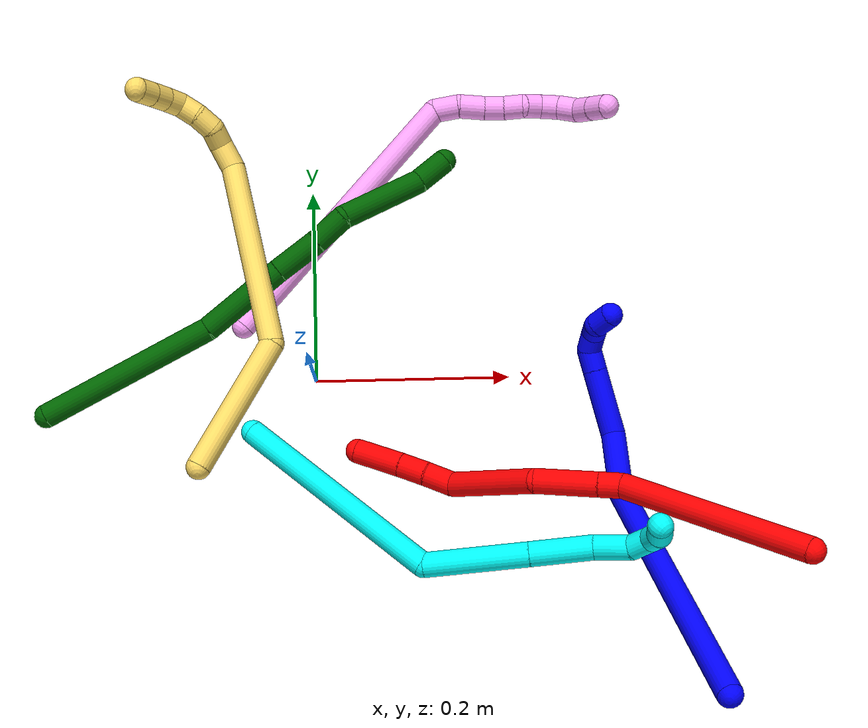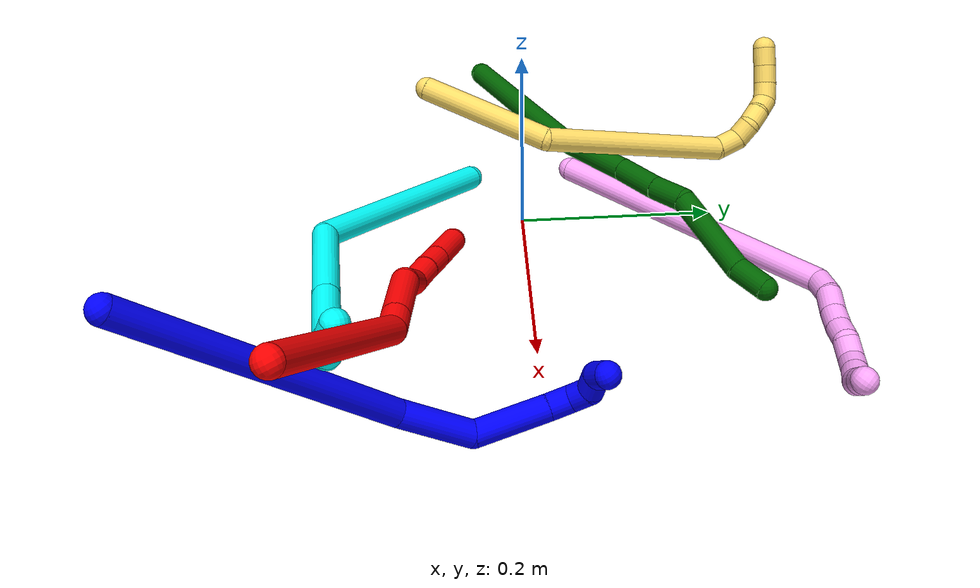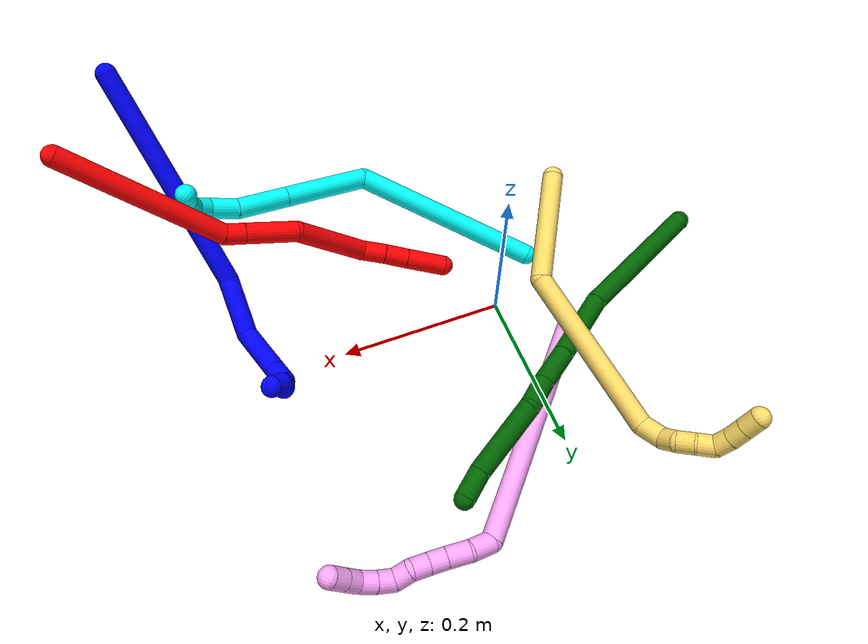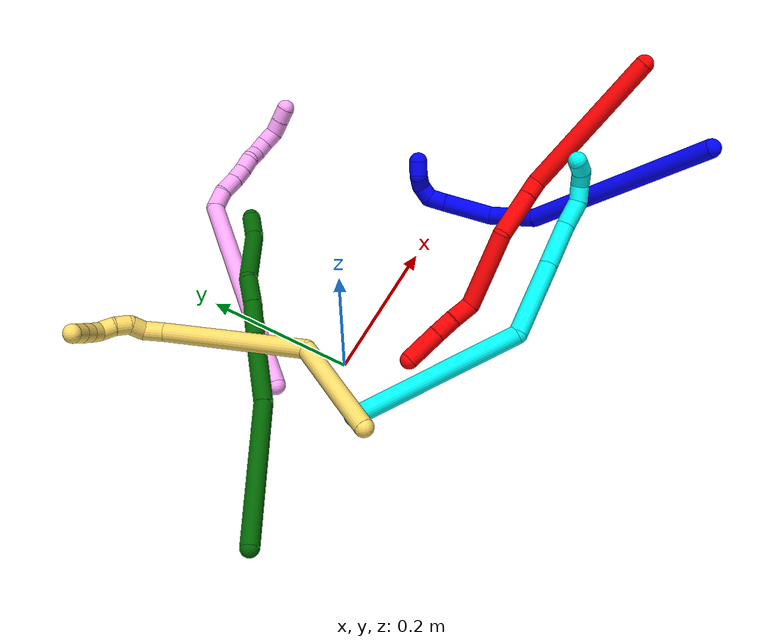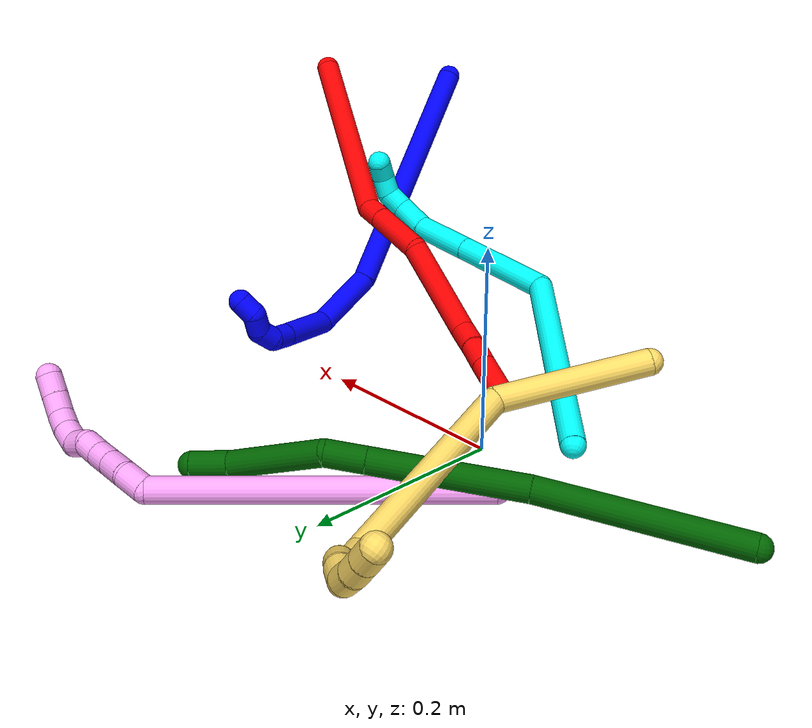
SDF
<sdf version="1.7">
 <world name="default">
  <plugin name="TubeGeneratorPlugin" filename="libtube_generator_plugin.so"/>
  <model name="photoneo_s_sensor">
   <static>1</static>
   <pose>0 0 2 1.57079 1.57079 3.14159</pose>
   <link name="link">
    <inertial><mass>0.1</mass></inertial>
    <sensor name="sensor" type="depth">
     <update_rate>30</update_rate>
     <camera>
      <horizontal_fov>1.22</horizontal_fov>
      <image><width>1920</width><height>1200</height><format>B8G8R8</format></image>
      <clip><near>0.1</near><far>4</far></clip>
      <depth_camera><output>points</output></depth_camera>
     </camera>
     <plugin name="camera_plugin" filename="libgazebo_ros_depth_camera.so">
      <baseline>0.2</baseline>
      <alwaysOn>1</alwaysOn>
      <updateRate>0.0</updateRate>
      <cameraName>camera_ir</cameraName>
      <imageTopicName>/camera/color/image_raw</imageTopicName>
      <cameraInfoTopicName>/camera/color/camera_info</cameraInfoTopicName>
      <depthImageTopicName>/camera/depth/image_raw</depthImageTopicName>
      <depthImageCameraInfoTopicName>/camera/depth/camera_info</depthImageCameraInfoTopicName>
      <pointCloudTopicName>/camera/depth/points</pointCloudTopicName>
      <frameName>fr_optical</frameName>
      <pointCloudCutoff>0.1</pointCloudCutoff>
      <pointCloudCutoffMax>2.0</pointCloudCutoffMax>
      <distortionK1>0</distortionK1>
      <distortionK2>0</distortionK2>
      <distortionK3>0</distortionK3>
      <distortionT1>0</distortionT1>
      <distortionT2>0</distortionT2>
      <CxPrime>0</CxPrime>
      <Cx>0</Cx>
      <Cy>0</Cy>
      <focalLength>0</focalLength>
      <hackBaseline>0</hackBaseline>
     </plugin>
    </sensor>
   </link>
  </model>
  <gravity>0 0 -9.8</gravity>
  <magnetic_field>6e-06 2.3e-05 -4.2e-05</magnetic_field>
  <atmosphere type="adiabatic"/>
  <physics name="default_physics" default="0" type="ode">
   <max_step_size>0.003</max_step_size>
   <real_time_factor>1</real_time_factor>
   <real_time_update_rate>1000</real_time_update_rate>
   <max_contacts>10000</max_contacts>
   <ode>
    <solver>
     <type>quick</type>
     <iters>100</iters>
     <sor>1.3</sor>
     <use_dynamic_moi_rescaling>0</use_dynamic_moi_rescaling>
    </solver>
    <constraints>
     <contact_max_correcting_vel>0</contact_max_correcting_vel>
     <contact_surface_layer>0.001</contact_surface_layer>
     <cfm>0</cfm>
     <erp>0.2</erp>
    </constraints>
   </ode>
  </physics>
  <scene><ambient>0.4 0.4 0.4 1</ambient><background>0.7 0.7 0.7 1</background><shadows>0</shadows></scene>
  <audio><device>default</device></audio>
  <spherical_coordinates>
   <surface_model>EARTH_WGS84</surface_model>
   <latitude_deg>0</latitude_deg>
   <longitude_deg>0</longitude_deg>
   <elevation>0</elevation>
   <heading_deg>0</heading_deg>
  </spherical_coordinates>
  <model name="bin">
   <static>1</static>
   <link name="bottom">
    <collision name="collision-bottom">
     <pose>0 0 -0.01 0 -0 0</pose>
     <geometry><box><size>0.8 0.6 0.02</size></box></geometry>
     <surface>
      <friction><ode><mu>100</mu><mu2>100</mu2></ode></friction>
      <contact><collide_bitmask>65535</collide_bitmask></contact>
     </surface>
    </collision>
   </link>
   <link name="west_wall">
    <collision name="collision-west_wall">
     <pose>-0.41 0 0.1 0 -0 0</pose>
     <geometry><box><size>0.02 0.6 0.2</size></box></geometry>
     <surface>
      <friction><ode><mu>100</mu><mu2>100</mu2></ode></friction>
      <contact><collide_bitmask>65535</collide_bitmask></contact>
     </surface>
    </collision>
   </link>
   <link name="east_wall">
    <collision name="collision-east_wall">
     <pose>0.41 0 0.1 0 -0 0</pose>
     <geometry><box><size>0.02 0.6 0.2</size></box></geometry>
     <surface>
      <friction><ode><mu>100</mu><mu2>100</mu2></ode></friction>
      <contact><collide_bitmask>65535</collide_bitmask></contact>
     </surface>
    </collision>
   </link>
   <link name="south_wall">
    <collision name="collision-south_wall">
     <pose>0 -0.31 0.1 0 -0 0</pose>
     <geometry><box><size>0.8 0.02 0.2</size></box></geometry>
     <surface>
      <friction><ode><mu>100</mu><mu2>100</mu2></ode></friction>
      <contact><collide_bitmask>65535</collide_bitmask></contact>
     </surface>
    </collision>
   </link>
   <link name="north_wall">
    <collision name="collision-north_wall">
     <pose>0 0.31 0.1 0 -0 0</pose>
     <geometry><box><size>0.8 0.02 0.2</size></box></geometry>
     <surface>
      <friction><ode><mu>100</mu><mu2>100</mu2></ode></friction>
      <contact><collide_bitmask>65535</collide_bitmask></contact>
     </surface>
    </collision>
   </link>
  </model>
  <model name="1">
   <static>0</static>
   <link name="1">
    <collision name="collision-cylinder-e_1_1_4">
     <pose>0.068487 -0.022817 0.118233 0.190639 0.517133 0.050564</pose>
     <geometry><cylinder><radius>0.0125</radius><length>0.277057</length></cylinder></geometry>
     <surface>
      <friction><ode><mu>1.16</mu><mu2>1.16</mu2><slip1>0</slip1><slip2>0</slip2></ode></friction>
      <contact><ode><kp>1e+06</kp><kd>1</kd><max_vel>0</max_vel><min_depth>0.001</min_depth></ode></contact>
     </surface>
    </collision>
    <visual name="visual-cylinder-e_1_1_4">
     <pose>0.068487 -0.022817 0.118233 0.190639 0.517133 0.050564</pose>
     <geometry><cylinder><radius>0.0125</radius><length>0.277057</length></cylinder></geometry>
     <material><ambient>0 0 1 1</ambient></material>
    </visual>
    <collision name="collision-cylinder-e_2_4_5">
     <pose>0.15716 -0.039245 0.265296 -0.218069 0.599624 -0.067654</pose>
     <geometry><cylinder><radius>0.0125</radius><length>0.071538</length></cylinder></geometry>
     <surface>
      <friction><ode><mu>1.16</mu><mu2>1.16</mu2><slip1>0</slip1><slip2>0</slip2></ode></friction>
      <contact><ode><kp>1e+06</kp><kd>1</kd><max_vel>0</max_vel><min_depth>0.001</min_depth></ode></contact>
     </surface>
    </collision>
    <visual name="visual-cylinder-e_2_4_5">
     <pose>0.15716 -0.039245 0.265296 -0.218069 0.599624 -0.067654</pose>
     <geometry><cylinder><radius>0.0125</radius><length>0.071538</length></cylinder></geometry>
     <material><ambient>0 0 1 1</ambient></material>
    </visual>
    <collision name="collision-cylinder-e_3_5_6">
     <pose>0.208787 -0.022091 0.303333 -0.863297 1.14748 -0.578648</pose>
     <geometry><cylinder><radius>0.0125</radius><length>0.068971</length></cylinder></geometry>
     <surface>
      <friction><ode><mu>1.16</mu><mu2>1.16</mu2><slip1>0</slip1><slip2>0</slip2></ode></friction>
      <contact><ode><kp>1e+06</kp><kd>1</kd><max_vel>0</max_vel><min_depth>0.001</min_depth></ode></contact>
     </surface>
    </collision>
    <visual name="visual-cylinder-e_3_5_6">
     <pose>0.208787 -0.022091 0.303333 -0.863297 1.14748 -0.578648</pose>
     <geometry><cylinder><radius>0.0125</radius><length>0.068971</length></cylinder></geometry>
     <material><ambient>0 0 1 1</ambient></material>
    </visual>
    <collision name="collision-cylinder-e_4_6_7">
     <pose>0.25038 -0.007744 0.31514 -0.942678 1.15973 -0.644359</pose>
     <geometry><cylinder><radius>0.0125</radius><length>0.022148</length></cylinder></geometry>
     <surface>
      <friction><ode><mu>1.16</mu><mu2>1.16</mu2><slip1>0</slip1><slip2>0</slip2></ode></friction>
      <contact><ode><kp>1e+06</kp><kd>1</kd><max_vel>0</max_vel><min_depth>0.001</min_depth></ode></contact>
     </surface>
    </collision>
    <visual name="visual-cylinder-e_4_6_7">
     <pose>0.25038 -0.007744 0.31514 -0.942678 1.15973 -0.644359</pose>
     <geometry><cylinder><radius>0.0125</radius><length>0.022148</length></cylinder></geometry>
     <material><ambient>0 0 1 1</ambient></material>
    </visual>
    <collision name="collision-cylinder-e_5_7_8">
     <pose>0.266692 0.003777 0.316395 -1.73861 0.653049 -0.762461</pose>
     <geometry><cylinder><radius>0.0125</radius><length>0.02028</length></cylinder></geometry>
     <surface>
      <friction><ode><mu>1.16</mu><mu2>1.16</mu2><slip1>0</slip1><slip2>0</slip2></ode></friction>
      <contact><ode><kp>1e+06</kp><kd>1</kd><max_vel>0</max_vel><min_depth>0.001</min_depth></ode></contact>
     </surface>
    </collision>
    <visual name="visual-cylinder-e_5_7_8">
     <pose>0.266692 0.003777 0.316395 -1.73861 0.653049 -0.762461</pose>
     <geometry><cylinder><radius>0.0125</radius><length>0.02028</length></cylinder></geometry>
     <material><ambient>0 0 1 1</ambient></material>
    </visual>
    <collision name="collision-cylinder-e_6_8_9">
     <pose>0.276778 0.01747 0.307872 -2.46601 0.403267 -1.05408</pose>
     <geometry><cylinder><radius>0.0125</radius><length>0.020003</length></cylinder></geometry>
     <surface>
      <friction><ode><mu>1.16</mu><mu2>1.16</mu2><slip1>0</slip1><slip2>0</slip2></ode></friction>
      <contact><ode><kp>1e+06</kp><kd>1</kd><max_vel>0</max_vel><min_depth>0.001</min_depth></ode></contact>
     </surface>
    </collision>
    <visual name="visual-cylinder-e_6_8_9">
     <pose>0.276778 0.01747 0.307872 -2.46601 0.403267 -1.05408</pose>
     <geometry><cylinder><radius>0.0125</radius><length>0.020003</length></cylinder></geometry>
     <material><ambient>0 0 1 1</ambient></material>
    </visual>
    <collision name="collision-cylinder-e_7_9_2">
     <pose>0.281309 0.032905 0.298263 -1.81667 0.060602 -0.077674</pose>
     <geometry><cylinder><radius>0.0125</radius><length>0.020003</length></cylinder></geometry>
     <surface>
      <friction><ode><mu>1.16</mu><mu2>1.16</mu2><slip1>0</slip1><slip2>0</slip2></ode></friction>
      <contact><ode><kp>1e+06</kp><kd>1</kd><max_vel>0</max_vel><min_depth>0.001</min_depth></ode></contact>
     </surface>
    </collision>
    <visual name="visual-cylinder-e_7_9_2">
     <pose>0.281309 0.032905 0.298263 -1.81667 0.060602 -0.077674</pose>
     <geometry><cylinder><radius>0.0125</radius><length>0.020003</length></cylinder></geometry>
     <material><ambient>0 0 1 1</ambient></material>
    </visual>
    <collision name="collision-sphere-2">
     <pose>0.281915 0.042588 0.295833 0 -0 0</pose>
     <geometry><sphere><radius>0.0125</radius></sphere></geometry>
     <surface>
      <friction><ode><mu>1.16</mu><mu2>1.16</mu2><slip1>0</slip1><slip2>0</slip2></ode></friction>
      <contact><ode><kp>1e+06</kp><kd>1</kd><max_vel>0</max_vel><min_depth>0.001</min_depth></ode></contact>
     </surface>
    </collision>
    <visual name="visual-sphere-2">
     <pose>0.281915 0.042588 0.295833 0 -0 0</pose>
     <geometry><sphere><radius>0.0125</radius></sphere></geometry>
     <material><ambient>0 0 1 1</ambient></material>
    </visual>
    <collision name="collision-sphere-9">
     <pose>0.280703 0.023222 0.300693 0 -0 0</pose>
     <geometry><sphere><radius>0.0125</radius></sphere></geometry>
     <surface>
      <friction><ode><mu>1.16</mu><mu2>1.16</mu2><slip1>0</slip1><slip2>0</slip2></ode></friction>
      <contact><ode><kp>1e+06</kp><kd>1</kd><max_vel>0</max_vel><min_depth>0.001</min_depth></ode></contact>
     </surface>
    </collision>
    <visual name="visual-sphere-9">
     <pose>0.280703 0.023222 0.300693 0 -0 0</pose>
     <geometry><sphere><radius>0.0125</radius></sphere></geometry>
     <material><ambient>0 0 1 1</ambient></material>
    </visual>
    <collision name="collision-sphere-4">
     <pose>0.136974 -0.045634 0.236466 0 -0 0</pose>
     <geometry><sphere><radius>0.0125</radius></sphere></geometry>
     <surface>
      <friction><ode><mu>1.16</mu><mu2>1.16</mu2><slip1>0</slip1><slip2>0</slip2></ode></friction>
      <contact><ode><kp>1e+06</kp><kd>1</kd><max_vel>0</max_vel><min_depth>0.001</min_depth></ode></contact>
     </surface>
    </collision>
    <visual name="visual-sphere-4">
     <pose>0.136974 -0.045634 0.236466 0 -0 0</pose>
     <geometry><sphere><radius>0.0125</radius></sphere></geometry>
     <material><ambient>0 0 1 1</ambient></material>
    </visual>
    <collision name="collision-sphere-1">
     <geometry><sphere><radius>0.0125</radius></sphere></geometry>
     <surface>
      <friction><ode><mu>1.16</mu><mu2>1.16</mu2><slip1>0</slip1><slip2>0</slip2></ode></friction>
      <contact><ode><kp>1e+06</kp><kd>1</kd><max_vel>0</max_vel><min_depth>0.001</min_depth></ode></contact>
     </surface>
    </collision>
    <visual name="visual-sphere-1">
     <geometry><sphere><radius>0.0125</radius></sphere></geometry>
     <material><ambient>0 0 1 1</ambient></material>
    </visual>
    <collision name="collision-sphere-8">
     <pose>0.272854 0.011717 0.31505 0 -0 0</pose>
     <geometry><sphere><radius>0.0125</radius></sphere></geometry>
     <surface>
      <friction><ode><mu>1.16</mu><mu2>1.16</mu2><slip1>0</slip1><slip2>0</slip2></ode></friction>
      <contact><ode><kp>1e+06</kp><kd>1</kd><max_vel>0</max_vel><min_depth>0.001</min_depth></ode></contact>
     </surface>
    </collision>
    <visual name="visual-sphere-8">
     <pose>0.272854 0.011717 0.31505 0 -0 0</pose>
     <geometry><sphere><radius>0.0125</radius></sphere></geometry>
     <material><ambient>0 0 1 1</ambient></material>
    </visual>
    <collision name="collision-sphere-5">
     <pose>0.177345 -0.032857 0.294125 0 -0 0</pose>
     <geometry><sphere><radius>0.0125</radius></sphere></geometry>
     <surface>
      <friction><ode><mu>1.16</mu><mu2>1.16</mu2><slip1>0</slip1><slip2>0</slip2></ode></friction>
      <contact><ode><kp>1e+06</kp><kd>1</kd><max_vel>0</max_vel><min_depth>0.001</min_depth></ode></contact>
     </surface>
    </collision>
    <visual name="visual-sphere-5">
     <pose>0.177345 -0.032857 0.294125 0 -0 0</pose>
     <geometry><sphere><radius>0.0125</radius></sphere></geometry>
     <material><ambient>0 0 1 1</ambient></material>
    </visual>
    <collision name="collision-sphere-6">
     <pose>0.240228 -0.011325 0.31254 0 -0 0</pose>
     <geometry><sphere><radius>0.0125</radius></sphere></geometry>
     <surface>
      <friction><ode><mu>1.16</mu><mu2>1.16</mu2><slip1>0</slip1><slip2>0</slip2></ode></friction>
      <contact><ode><kp>1e+06</kp><kd>1</kd><max_vel>0</max_vel><min_depth>0.001</min_depth></ode></contact>
     </surface>
    </collision>
    <visual name="visual-sphere-6">
     <pose>0.240228 -0.011325 0.31254 0 -0 0</pose>
     <geometry><sphere><radius>0.0125</radius></sphere></geometry>
     <material><ambient>0 0 1 1</ambient></material>
    </visual>
    <collision name="collision-sphere-7">
     <pose>0.260531 -0.004164 0.31774 0 -0 0</pose>
     <geometry><sphere><radius>0.0125</radius></sphere></geometry>
     <surface>
      <friction><ode><mu>1.16</mu><mu2>1.16</mu2><slip1>0</slip1><slip2>0</slip2></ode></friction>
      <contact><ode><kp>1e+06</kp><kd>1</kd><max_vel>0</max_vel><min_depth>0.001</min_depth></ode></contact>
     </surface>
    </collision>
    <visual name="visual-sphere-7">
     <pose>0.260531 -0.004164 0.31774 0 -0 0</pose>
     <geometry><sphere><radius>0.0125</radius></sphere></geometry>
     <material><ambient>0 0 1 1</ambient></material>
    </visual>
    <inertial>
     <pose>0.133471 -0.01948 0.196356 0 -0 0</pose>
     <mass>0.5</mass>
     <inertia>
      <ixx>0.001678</ixx>
      <ixy>0</ixy>
      <ixz>0</ixz>
      <iyy>0.001889</iyy>
      <iyz>0</iyz>
      <izz>-0.000633</izz>
     </inertia>
    </inertial>
   </link>
   <pose>0.369768 -0.318902 0.234866 2.65435 -0.247799 2.24525</pose>
  </model>
  <model name="2">
   <static>0</static>
   <link name="2">
    <collision name="collision-cylinder-e_1_1_4">
     <pose>-0.09896 0.009844 0.02065 -0.444846 -1.34361 0.355888</pose>
     <geometry><cylinder><radius>0.0125</radius><length>0.20314</length></cylinder></geometry>
     <surface>
      <friction><ode><mu>1.16</mu><mu2>1.16</mu2><slip1>0</slip1><slip2>0</slip2></ode></friction>
      <contact><ode><kp>1e+06</kp><kd>1</kd><max_vel>0</max_vel><min_depth>0.001</min_depth></ode></contact>
     </surface>
    </collision>
    <visual name="visual-cylinder-e_1_1_4">
     <pose>-0.09896 0.009844 0.02065 -0.444846 -1.34361 0.355888</pose>
     <geometry><cylinder><radius>0.0125</radius><length>0.20314</length></cylinder></geometry>
     <material><ambient>1 0 0 1</ambient></material>
    </visual>
    <collision name="collision-cylinder-e_2_4_5">
     <pose>-0.208937 0.021377 0.038067 -2.66032 -1.25105 2.48657</pose>
     <geometry><cylinder><radius>0.0125</radius><length>0.02321</length></cylinder></geometry>
     <surface>
      <friction><ode><mu>1.16</mu><mu2>1.16</mu2><slip1>0</slip1><slip2>0</slip2></ode></friction>
      <contact><ode><kp>1e+06</kp><kd>1</kd><max_vel>0</max_vel><min_depth>0.001</min_depth></ode></contact>
     </surface>
    </collision>
    <visual name="visual-cylinder-e_2_4_5">
     <pose>-0.208937 0.021377 0.038067 -2.66032 -1.25105 2.48657</pose>
     <geometry><cylinder><radius>0.0125</radius><length>0.02321</length></cylinder></geometry>
     <material><ambient>1 0 0 1</ambient></material>
    </visual>
    <collision name="collision-cylinder-e_3_5_6">
     <pose>-0.24988 0.027774 0.02658 -2.62326 -1.26335 2.44631</pose>
     <geometry><cylinder><radius>0.0125</radius><length>0.062798</length></cylinder></geometry>
     <surface>
      <friction><ode><mu>1.16</mu><mu2>1.16</mu2><slip1>0</slip1><slip2>0</slip2></ode></friction>
      <contact><ode><kp>1e+06</kp><kd>1</kd><max_vel>0</max_vel><min_depth>0.001</min_depth></ode></contact>
     </surface>
    </collision>
    <visual name="visual-cylinder-e_3_5_6">
     <pose>-0.24988 0.027774 0.02658 -2.62326 -1.26335 2.44631</pose>
     <geometry><cylinder><radius>0.0125</radius><length>0.062798</length></cylinder></geometry>
     <material><ambient>1 0 0 1</ambient></material>
    </visual>
    <collision name="collision-cylinder-e_4_6_7">
     <pose>-0.326328 0.052956 0.025137 -1.24967 -1.1365 0.863118</pose>
     <geometry><cylinder><radius>0.0125</radius><length>0.102564</length></cylinder></geometry>
     <surface>
      <friction><ode><mu>1.16</mu><mu2>1.16</mu2><slip1>0</slip1><slip2>0</slip2></ode></friction>
      <contact><ode><kp>1e+06</kp><kd>1</kd><max_vel>0</max_vel><min_depth>0.001</min_depth></ode></contact>
     </surface>
    </collision>
    <visual name="visual-cylinder-e_4_6_7">
     <pose>-0.326328 0.052956 0.025137 -1.24967 -1.1365 0.863118</pose>
     <geometry><cylinder><radius>0.0125</radius><length>0.102564</length></cylinder></geometry>
     <material><ambient>1 0 0 1</ambient></material>
    </visual>
    <collision name="collision-cylinder-e_5_7_8">
     <pose>-0.387399 0.07151 0.029731 2.42762 -1.37183 -2.28647</pose>
     <geometry><cylinder><radius>0.0125</radius><length>0.029684</length></cylinder></geometry>
     <surface>
      <friction><ode><mu>1.16</mu><mu2>1.16</mu2><slip1>0</slip1><slip2>0</slip2></ode></friction>
      <contact><ode><kp>1e+06</kp><kd>1</kd><max_vel>0</max_vel><min_depth>0.001</min_depth></ode></contact>
     </surface>
    </collision>
    <visual name="visual-cylinder-e_5_7_8">
     <pose>-0.387399 0.07151 0.029731 2.42762 -1.37183 -2.28647</pose>
     <geometry><cylinder><radius>0.0125</radius><length>0.029684</length></cylinder></geometry>
     <material><ambient>1 0 0 1</ambient></material>
    </visual>
    <collision name="collision-cylinder-e_6_8_9">
     <pose>-0.41621 0.068749 0.026382 2.50307 -1.47228 -2.4419</pose>
     <geometry><cylinder><radius>0.0125</radius><length>0.028663</length></cylinder></geometry>
     <surface>
      <friction><ode><mu>1.16</mu><mu2>1.16</mu2><slip1>0</slip1><slip2>0</slip2></ode></friction>
      <contact><ode><kp>1e+06</kp><kd>1</kd><max_vel>0</max_vel><min_depth>0.001</min_depth></ode></contact>
     </surface>
    </collision>
    <visual name="visual-cylinder-e_6_8_9">
     <pose>-0.41621 0.068749 0.026382 2.50307 -1.47228 -2.4419</pose>
     <geometry><cylinder><radius>0.0125</radius><length>0.028663</length></cylinder></geometry>
     <material><ambient>1 0 0 1</ambient></material>
    </visual>
    <collision name="collision-cylinder-e_7_9_2">
     <pose>-0.45533 0.067097 0.023027 2.79126 -1.47589 -2.75714</pose>
     <geometry><cylinder><radius>0.0125</radius><length>0.049942</length></cylinder></geometry>
     <surface>
      <friction><ode><mu>1.16</mu><mu2>1.16</mu2><slip1>0</slip1><slip2>0</slip2></ode></friction>
      <contact><ode><kp>1e+06</kp><kd>1</kd><max_vel>0</max_vel><min_depth>0.001</min_depth></ode></contact>
     </surface>
    </collision>
    <visual name="visual-cylinder-e_7_9_2">
     <pose>-0.45533 0.067097 0.023027 2.79126 -1.47589 -2.75714</pose>
     <geometry><cylinder><radius>0.0125</radius><length>0.049942</length></cylinder></geometry>
     <material><ambient>1 0 0 1</ambient></material>
    </visual>
    <collision name="collision-sphere-2">
     <pose>-0.480189 0.066285 0.020805 0 -0 0</pose>
     <geometry><sphere><radius>0.0125</radius></sphere></geometry>
     <surface>
      <friction><ode><mu>1.16</mu><mu2>1.16</mu2><slip1>0</slip1><slip2>0</slip2></ode></friction>
      <contact><ode><kp>1e+06</kp><kd>1</kd><max_vel>0</max_vel><min_depth>0.001</min_depth></ode></contact>
     </surface>
    </collision>
    <visual name="visual-sphere-2">
     <pose>-0.480189 0.066285 0.020805 0 -0 0</pose>
     <geometry><sphere><radius>0.0125</radius></sphere></geometry>
     <material><ambient>1 0 0 1</ambient></material>
    </visual>
    <collision name="collision-sphere-9">
     <pose>-0.430471 0.067909 0.02525 0 -0 0</pose>
     <geometry><sphere><radius>0.0125</radius></sphere></geometry>
     <surface>
      <friction><ode><mu>1.16</mu><mu2>1.16</mu2><slip1>0</slip1><slip2>0</slip2></ode></friction>
      <contact><ode><kp>1e+06</kp><kd>1</kd><max_vel>0</max_vel><min_depth>0.001</min_depth></ode></contact>
     </surface>
    </collision>
    <visual name="visual-sphere-9">
     <pose>-0.430471 0.067909 0.02525 0 -0 0</pose>
     <geometry><sphere><radius>0.0125</radius></sphere></geometry>
     <material><ambient>1 0 0 1</ambient></material>
    </visual>
    <collision name="collision-sphere-4">
     <pose>-0.19792 0.019689 0.041301 0 -0 0</pose>
     <geometry><sphere><radius>0.0125</radius></sphere></geometry>
     <surface>
      <friction><ode><mu>1.16</mu><mu2>1.16</mu2><slip1>0</slip1><slip2>0</slip2></ode></friction>
      <contact><ode><kp>1e+06</kp><kd>1</kd><max_vel>0</max_vel><min_depth>0.001</min_depth></ode></contact>
     </surface>
    </collision>
    <visual name="visual-sphere-4">
     <pose>-0.19792 0.019689 0.041301 0 -0 0</pose>
     <geometry><sphere><radius>0.0125</radius></sphere></geometry>
     <material><ambient>1 0 0 1</ambient></material>
    </visual>
    <collision name="collision-sphere-1">
     <geometry><sphere><radius>0.0125</radius></sphere></geometry>
     <surface>
      <friction><ode><mu>1.16</mu><mu2>1.16</mu2><slip1>0</slip1><slip2>0</slip2></ode></friction>
      <contact><ode><kp>1e+06</kp><kd>1</kd><max_vel>0</max_vel><min_depth>0.001</min_depth></ode></contact>
     </surface>
    </collision>
    <visual name="visual-sphere-1">
     <geometry><sphere><radius>0.0125</radius></sphere></geometry>
     <material><ambient>1 0 0 1</ambient></material>
    </visual>
    <collision name="collision-sphere-8">
     <pose>-0.401948 0.069589 0.027513 0 -0 0</pose>
     <geometry><sphere><radius>0.0125</radius></sphere></geometry>
     <surface>
      <friction><ode><mu>1.16</mu><mu2>1.16</mu2><slip1>0</slip1><slip2>0</slip2></ode></friction>
      <contact><ode><kp>1e+06</kp><kd>1</kd><max_vel>0</max_vel><min_depth>0.001</min_depth></ode></contact>
     </surface>
    </collision>
    <visual name="visual-sphere-8">
     <pose>-0.401948 0.069589 0.027513 0 -0 0</pose>
     <geometry><sphere><radius>0.0125</radius></sphere></geometry>
     <material><ambient>1 0 0 1</ambient></material>
    </visual>
    <collision name="collision-sphere-5">
     <pose>-0.219954 0.023066 0.034834 0 -0 0</pose>
     <geometry><sphere><radius>0.0125</radius></sphere></geometry>
     <surface>
      <friction><ode><mu>1.16</mu><mu2>1.16</mu2><slip1>0</slip1><slip2>0</slip2></ode></friction>
      <contact><ode><kp>1e+06</kp><kd>1</kd><max_vel>0</max_vel><min_depth>0.001</min_depth></ode></contact>
     </surface>
    </collision>
    <visual name="visual-sphere-5">
     <pose>-0.219954 0.023066 0.034834 0 -0 0</pose>
     <geometry><sphere><radius>0.0125</radius></sphere></geometry>
     <material><ambient>1 0 0 1</ambient></material>
    </visual>
    <collision name="collision-sphere-6">
     <pose>-0.279807 0.032481 0.018326 0 -0 0</pose>
     <geometry><sphere><radius>0.0125</radius></sphere></geometry>
     <surface>
      <friction><ode><mu>1.16</mu><mu2>1.16</mu2><slip1>0</slip1><slip2>0</slip2></ode></friction>
      <contact><ode><kp>1e+06</kp><kd>1</kd><max_vel>0</max_vel><min_depth>0.001</min_depth></ode></contact>
     </surface>
    </collision>
    <visual name="visual-sphere-6">
     <pose>-0.279807 0.032481 0.018326 0 -0 0</pose>
     <geometry><sphere><radius>0.0125</radius></sphere></geometry>
     <material><ambient>1 0 0 1</ambient></material>
    </visual>
    <collision name="collision-sphere-7">
     <pose>-0.37285 0.073431 0.031948 0 -0 0</pose>
     <geometry><sphere><radius>0.0125</radius></sphere></geometry>
     <surface>
      <friction><ode><mu>1.16</mu><mu2>1.16</mu2><slip1>0</slip1><slip2>0</slip2></ode></friction>
      <contact><ode><kp>1e+06</kp><kd>1</kd><max_vel>0</max_vel><min_depth>0.001</min_depth></ode></contact>
     </surface>
    </collision>
    <visual name="visual-sphere-7">
     <pose>-0.37285 0.073431 0.031948 0 -0 0</pose>
     <geometry><sphere><radius>0.0125</radius></sphere></geometry>
     <material><ambient>1 0 0 1</ambient></material>
    </visual>
    <inertial>
     <pose>-0.240566 0.034231 0.024229 0 -0 0</pose>
     <mass>0.5</mass>
     <inertia>
      <ixx>0.000219</ixx>
      <ixy>0</ixy>
      <ixz>0</ixz>
      <iyy>0.000919</iyy>
      <iyz>0</iyz>
      <izz>0.000709</izz>
     </inertia>
    </inertial>
   </link>
   <pose>0.445884 -0.195251 0.251449 -2.52744 -0.403785 -0.390455</pose>
  </model>
  <model name="3">
   <static>0</static>
   <link name="3">
    <collision name="collision-cylinder-e_1_1_4">
     <pose>0.024534 0.011655 0.112837 -0.102924 0.212995 -0.011012</pose>
     <geometry><cylinder><radius>0.0125</radius><length>0.232121</length></cylinder></geometry>
     <surface>
      <friction><ode><mu>1.16</mu><mu2>1.16</mu2><slip1>0</slip1><slip2>0</slip2></ode></friction>
      <contact><ode><kp>1e+06</kp><kd>1</kd><max_vel>0</max_vel><min_depth>0.001</min_depth></ode></contact>
     </surface>
    </collision>
    <visual name="visual-cylinder-e_1_1_4">
     <pose>0.024534 0.011655 0.112837 -0.102924 0.212995 -0.011012</pose>
     <geometry><cylinder><radius>0.0125</radius><length>0.232121</length></cylinder></geometry>
     <material><ambient>0.003922 1 0.996078 1</ambient></material>
    </visual>
    <collision name="collision-cylinder-e_2_4_5">
     <pose>0.076383 0.056829 0.255182 -0.848973 0.548963 -0.253175</pose>
     <geometry><cylinder><radius>0.0125</radius><length>0.104696</length></cylinder></geometry>
     <surface>
      <friction><ode><mu>1.16</mu><mu2>1.16</mu2><slip1>0</slip1><slip2>0</slip2></ode></friction>
      <contact><ode><kp>1e+06</kp><kd>1</kd><max_vel>0</max_vel><min_depth>0.001</min_depth></ode></contact>
     </surface>
    </collision>
    <visual name="visual-cylinder-e_2_4_5">
     <pose>0.076383 0.056829 0.255182 -0.848973 0.548963 -0.253175</pose>
     <geometry><cylinder><radius>0.0125</radius><length>0.104696</length></cylinder></geometry>
     <material><ambient>0.003922 1 0.996078 1</ambient></material>
    </visual>
    <collision name="collision-cylinder-e_3_5_6">
     <pose>0.120147 0.110786 0.302483 -0.854414 0.545549 -0.253343</pose>
     <geometry><cylinder><radius>0.0125</radius><length>0.063401</length></cylinder></geometry>
     <surface>
      <friction><ode><mu>1.16</mu><mu2>1.16</mu2><slip1>0</slip1><slip2>0</slip2></ode></friction>
      <contact><ode><kp>1e+06</kp><kd>1</kd><max_vel>0</max_vel><min_depth>0.001</min_depth></ode></contact>
     </surface>
    </collision>
    <visual name="visual-cylinder-e_3_5_6">
     <pose>0.120147 0.110786 0.302483 -0.854414 0.545549 -0.253343</pose>
     <geometry><cylinder><radius>0.0125</radius><length>0.063401</length></cylinder></geometry>
     <material><ambient>0.003922 1 0.996078 1</ambient></material>
    </visual>
    <collision name="collision-cylinder-e_4_6_7">
     <pose>0.141994 0.143017 0.333309 -0.735586 0.297945 -0.115534</pose>
     <geometry><cylinder><radius>0.0125</radius><length>0.036771</length></cylinder></geometry>
     <surface>
      <friction><ode><mu>1.16</mu><mu2>1.16</mu2><slip1>0</slip1><slip2>0</slip2></ode></friction>
      <contact><ode><kp>1e+06</kp><kd>1</kd><max_vel>0</max_vel><min_depth>0.001</min_depth></ode></contact>
     </surface>
    </collision>
    <visual name="visual-cylinder-e_4_6_7">
     <pose>0.141994 0.143017 0.333309 -0.735586 0.297945 -0.115534</pose>
     <geometry><cylinder><radius>0.0125</radius><length>0.036771</length></cylinder></geometry>
     <material><ambient>0.003922 1 0.996078 1</ambient></material>
    </visual>
    <collision name="collision-cylinder-e_5_7_8">
     <pose>0.147371 0.164909 0.351416 -1.10509 -0.001762 0.001087</pose>
     <geometry><cylinder><radius>0.0125</radius><length>0.022604</length></cylinder></geometry>
     <surface>
      <friction><ode><mu>1.16</mu><mu2>1.16</mu2><slip1>0</slip1><slip2>0</slip2></ode></friction>
      <contact><ode><kp>1e+06</kp><kd>1</kd><max_vel>0</max_vel><min_depth>0.001</min_depth></ode></contact>
     </surface>
    </collision>
    <visual name="visual-cylinder-e_5_7_8">
     <pose>0.147371 0.164909 0.351416 -1.10509 -0.001762 0.001087</pose>
     <geometry><cylinder><radius>0.0125</radius><length>0.022604</length></cylinder></geometry>
     <material><ambient>0.003922 1 0.996078 1</ambient></material>
    </visual>
    <collision name="collision-cylinder-e_6_8_9">
     <pose>0.141909 0.182281 0.36112 -1.00403 -0.563066 0.314883</pose>
     <geometry><cylinder><radius>0.0125</radius><length>0.02039</length></cylinder></geometry>
     <surface>
      <friction><ode><mu>1.16</mu><mu2>1.16</mu2><slip1>0</slip1><slip2>0</slip2></ode></friction>
      <contact><ode><kp>1e+06</kp><kd>1</kd><max_vel>0</max_vel><min_depth>0.001</min_depth></ode></contact>
     </surface>
    </collision>
    <visual name="visual-cylinder-e_6_8_9">
     <pose>0.141909 0.182281 0.36112 -1.00403 -0.563066 0.314883</pose>
     <geometry><cylinder><radius>0.0125</radius><length>0.02039</length></cylinder></geometry>
     <material><ambient>0.003922 1 0.996078 1</ambient></material>
    </visual>
    <collision name="collision-cylinder-e_7_9_2">
     <pose>0.129091 0.196284 0.366429 -1.47004 -0.828667 0.756824</pose>
     <geometry><cylinder><radius>0.0125</radius><length>0.020016</length></cylinder></geometry>
     <surface>
      <friction><ode><mu>1.16</mu><mu2>1.16</mu2><slip1>0</slip1><slip2>0</slip2></ode></friction>
      <contact><ode><kp>1e+06</kp><kd>1</kd><max_vel>0</max_vel><min_depth>0.001</min_depth></ode></contact>
     </surface>
    </collision>
    <visual name="visual-cylinder-e_7_9_2">
     <pose>0.129091 0.196284 0.366429 -1.47004 -0.828667 0.756824</pose>
     <geometry><cylinder><radius>0.0125</radius><length>0.020016</length></cylinder></geometry>
     <material><ambient>0.003922 1 0.996078 1</ambient></material>
    </visual>
    <collision name="collision-sphere-2">
     <pose>0.121714 0.203013 0.36711 0 -0 0</pose>
     <geometry><sphere><radius>0.0125</radius></sphere></geometry>
     <surface>
      <friction><ode><mu>1.16</mu><mu2>1.16</mu2><slip1>0</slip1><slip2>0</slip2></ode></friction>
      <contact><ode><kp>1e+06</kp><kd>1</kd><max_vel>0</max_vel><min_depth>0.001</min_depth></ode></contact>
     </surface>
    </collision>
    <visual name="visual-sphere-2">
     <pose>0.121714 0.203013 0.36711 0 -0 0</pose>
     <geometry><sphere><radius>0.0125</radius></sphere></geometry>
     <material><ambient>0.003922 1 0.996078 1</ambient></material>
    </visual>
    <collision name="collision-sphere-9">
     <pose>0.136467 0.189554 0.365749 0 -0 0</pose>
     <geometry><sphere><radius>0.0125</radius></sphere></geometry>
     <surface>
      <friction><ode><mu>1.16</mu><mu2>1.16</mu2><slip1>0</slip1><slip2>0</slip2></ode></friction>
      <contact><ode><kp>1e+06</kp><kd>1</kd><max_vel>0</max_vel><min_depth>0.001</min_depth></ode></contact>
     </surface>
    </collision>
    <visual name="visual-sphere-9">
     <pose>0.136467 0.189554 0.365749 0 -0 0</pose>
     <geometry><sphere><radius>0.0125</radius></sphere></geometry>
     <material><ambient>0.003922 1 0.996078 1</ambient></material>
    </visual>
    <collision name="collision-sphere-4">
     <pose>0.049068 0.02331 0.225675 0 -0 0</pose>
     <geometry><sphere><radius>0.0125</radius></sphere></geometry>
     <surface>
      <friction><ode><mu>1.16</mu><mu2>1.16</mu2><slip1>0</slip1><slip2>0</slip2></ode></friction>
      <contact><ode><kp>1e+06</kp><kd>1</kd><max_vel>0</max_vel><min_depth>0.001</min_depth></ode></contact>
     </surface>
    </collision>
    <visual name="visual-sphere-4">
     <pose>0.049068 0.02331 0.225675 0 -0 0</pose>
     <geometry><sphere><radius>0.0125</radius></sphere></geometry>
     <material><ambient>0.003922 1 0.996078 1</ambient></material>
    </visual>
    <collision name="collision-sphere-1">
     <geometry><sphere><radius>0.0125</radius></sphere></geometry>
     <surface>
      <friction><ode><mu>1.16</mu><mu2>1.16</mu2><slip1>0</slip1><slip2>0</slip2></ode></friction>
      <contact><ode><kp>1e+06</kp><kd>1</kd><max_vel>0</max_vel><min_depth>0.001</min_depth></ode></contact>
     </surface>
    </collision>
    <visual name="visual-sphere-1">
     <geometry><sphere><radius>0.0125</radius></sphere></geometry>
     <material><ambient>0.003922 1 0.996078 1</ambient></material>
    </visual>
    <collision name="collision-sphere-8">
     <pose>0.147351 0.175007 0.356491 0 -0 0</pose>
     <geometry><sphere><radius>0.0125</radius></sphere></geometry>
     <surface>
      <friction><ode><mu>1.16</mu><mu2>1.16</mu2><slip1>0</slip1><slip2>0</slip2></ode></friction>
      <contact><ode><kp>1e+06</kp><kd>1</kd><max_vel>0</max_vel><min_depth>0.001</min_depth></ode></contact>
     </surface>
    </collision>
    <visual name="visual-sphere-8">
     <pose>0.147351 0.175007 0.356491 0 -0 0</pose>
     <geometry><sphere><radius>0.0125</radius></sphere></geometry>
     <material><ambient>0.003922 1 0.996078 1</ambient></material>
    </visual>
    <collision name="collision-sphere-5">
     <pose>0.103698 0.090348 0.284689 0 -0 0</pose>
     <geometry><sphere><radius>0.0125</radius></sphere></geometry>
     <surface>
      <friction><ode><mu>1.16</mu><mu2>1.16</mu2><slip1>0</slip1><slip2>0</slip2></ode></friction>
      <contact><ode><kp>1e+06</kp><kd>1</kd><max_vel>0</max_vel><min_depth>0.001</min_depth></ode></contact>
     </surface>
    </collision>
    <visual name="visual-sphere-5">
     <pose>0.103698 0.090348 0.284689 0 -0 0</pose>
     <geometry><sphere><radius>0.0125</radius></sphere></geometry>
     <material><ambient>0.003922 1 0.996078 1</ambient></material>
    </visual>
    <collision name="collision-sphere-6">
     <pose>0.136596 0.131223 0.320278 0 -0 0</pose>
     <geometry><sphere><radius>0.0125</radius></sphere></geometry>
     <surface>
      <friction><ode><mu>1.16</mu><mu2>1.16</mu2><slip1>0</slip1><slip2>0</slip2></ode></friction>
      <contact><ode><kp>1e+06</kp><kd>1</kd><max_vel>0</max_vel><min_depth>0.001</min_depth></ode></contact>
     </surface>
    </collision>
    <visual name="visual-sphere-6">
     <pose>0.136596 0.131223 0.320278 0 -0 0</pose>
     <geometry><sphere><radius>0.0125</radius></sphere></geometry>
     <material><ambient>0.003922 1 0.996078 1</ambient></material>
    </visual>
    <collision name="collision-sphere-7">
     <pose>0.147391 0.154811 0.346341 0 -0 0</pose>
     <geometry><sphere><radius>0.0125</radius></sphere></geometry>
     <surface>
      <friction><ode><mu>1.16</mu><mu2>1.16</mu2><slip1>0</slip1><slip2>0</slip2></ode></friction>
      <contact><ode><kp>1e+06</kp><kd>1</kd><max_vel>0</max_vel><min_depth>0.001</min_depth></ode></contact>
     </surface>
    </collision>
    <visual name="visual-sphere-7">
     <pose>0.147391 0.154811 0.346341 0 -0 0</pose>
     <geometry><sphere><radius>0.0125</radius></sphere></geometry>
     <material><ambient>0.003922 1 0.996078 1</ambient></material>
    </visual>
    <inertial>
     <pose>0.070678 0.064622 0.213968 0 -0 0</pose>
     <mass>0.5</mass>
     <inertia>
      <ixx>0.001111</ixx>
      <ixy>0</ixy>
      <ixz>0</ixz>
      <iyy>0.001122</iyy>
      <iyz>0</iyz>
      <izz>-0.00045</izz>
     </inertia>
    </inertial>
   </link>
   <pose>-0.065688 -0.052265 0.011787 0.869499 0.876268 0.091179</pose>
  </model>
  <model name="4">
   <static>0</static>
   <link name="4">
    <collision name="collision-cylinder-e_1_1_4">
     <pose>-0.03721 -0.024929 0.145551 0.169625 -0.246838 -0.021092</pose>
     <geometry><cylinder><radius>0.0125</radius><length>0.304573</length></cylinder></geometry>
     <surface>
      <friction><ode><mu>1.16</mu><mu2>1.16</mu2><slip1>0</slip1><slip2>0</slip2></ode></friction>
      <contact><ode><kp>1e+06</kp><kd>1</kd><max_vel>0</max_vel><min_depth>0.001</min_depth></ode></contact>
     </surface>
    </collision>
    <visual name="visual-cylinder-e_1_1_4">
     <pose>-0.03721 -0.024929 0.145551 0.169625 -0.246838 -0.021092</pose>
     <geometry><cylinder><radius>0.0125</radius><length>0.304573</length></cylinder></geometry>
     <material><ambient>1 0.65098 0.996078 1</ambient></material>
    </visual>
    <collision name="collision-cylinder-e_2_4_5">
     <pose>-0.074835 -0.060305 0.299419 0.89851 -0.03112 -0.015005</pose>
     <geometry><cylinder><radius>0.0125</radius><length>0.026719</length></cylinder></geometry>
     <surface>
      <friction><ode><mu>1.16</mu><mu2>1.16</mu2><slip1>0</slip1><slip2>0</slip2></ode></friction>
      <contact><ode><kp>1e+06</kp><kd>1</kd><max_vel>0</max_vel><min_depth>0.001</min_depth></ode></contact>
     </surface>
    </collision>
    <visual name="visual-cylinder-e_2_4_5">
     <pose>-0.074835 -0.060305 0.299419 0.89851 -0.03112 -0.015005</pose>
     <geometry><cylinder><radius>0.0125</radius><length>0.026719</length></cylinder></geometry>
     <material><ambient>1 0.65098 0.996078 1</ambient></material>
    </visual>
    <collision name="collision-cylinder-e_3_5_6">
     <pose>-0.071691 -0.081158 0.315213 0.947619 0.270937 0.139557</pose>
     <geometry><cylinder><radius>0.0125</radius><length>0.026598</length></cylinder></geometry>
     <surface>
      <friction><ode><mu>1.16</mu><mu2>1.16</mu2><slip1>0</slip1><slip2>0</slip2></ode></friction>
      <contact><ode><kp>1e+06</kp><kd>1</kd><max_vel>0</max_vel><min_depth>0.001</min_depth></ode></contact>
     </surface>
    </collision>
    <visual name="visual-cylinder-e_3_5_6">
     <pose>-0.071691 -0.081158 0.315213 0.947619 0.270937 0.139557</pose>
     <geometry><cylinder><radius>0.0125</radius><length>0.026598</length></cylinder></geometry>
     <material><ambient>1 0.65098 0.996078 1</ambient></material>
    </visual>
    <collision name="collision-cylinder-e_4_6_7">
     <pose>-0.066234 -0.099796 0.32885 0.928562 0.182566 0.091618</pose>
     <geometry><cylinder><radius>0.0125</radius><length>0.02091</length></cylinder></geometry>
     <surface>
      <friction><ode><mu>1.16</mu><mu2>1.16</mu2><slip1>0</slip1><slip2>0</slip2></ode></friction>
      <contact><ode><kp>1e+06</kp><kd>1</kd><max_vel>0</max_vel><min_depth>0.001</min_depth></ode></contact>
     </surface>
    </collision>
    <visual name="visual-cylinder-e_4_6_7">
     <pose>-0.066234 -0.099796 0.32885 0.928562 0.182566 0.091618</pose>
     <geometry><cylinder><radius>0.0125</radius><length>0.02091</length></cylinder></geometry>
     <material><ambient>1 0.65098 0.996078 1</ambient></material>
    </visual>
    <collision name="collision-cylinder-e_5_7_8">
     <pose>-0.063882 -0.116203 0.340917 0.944931 0.044968 0.022985</pose>
     <geometry><cylinder><radius>0.0125</radius><length>0.020193</length></cylinder></geometry>
     <surface>
      <friction><ode><mu>1.16</mu><mu2>1.16</mu2><slip1>0</slip1><slip2>0</slip2></ode></friction>
      <contact><ode><kp>1e+06</kp><kd>1</kd><max_vel>0</max_vel><min_depth>0.001</min_depth></ode></contact>
     </surface>
    </collision>
    <visual name="visual-cylinder-e_5_7_8">
     <pose>-0.063882 -0.116203 0.340917 0.944931 0.044968 0.022985</pose>
     <geometry><cylinder><radius>0.0125</radius><length>0.020193</length></cylinder></geometry>
     <material><ambient>1 0.65098 0.996078 1</ambient></material>
    </visual>
    <collision name="collision-cylinder-e_6_8_9">
     <pose>-0.058789 -0.129336 0.354289 0.5864 0.477699 0.146761</pose>
     <geometry><cylinder><radius>0.0125</radius><length>0.02018</length></cylinder></geometry>
     <surface>
      <friction><ode><mu>1.16</mu><mu2>1.16</mu2><slip1>0</slip1><slip2>0</slip2></ode></friction>
      <contact><ode><kp>1e+06</kp><kd>1</kd><max_vel>0</max_vel><min_depth>0.001</min_depth></ode></contact>
     </surface>
    </collision>
    <visual name="visual-cylinder-e_6_8_9">
     <pose>-0.058789 -0.129336 0.354289 0.5864 0.477699 0.146761</pose>
     <geometry><cylinder><radius>0.0125</radius><length>0.02018</length></cylinder></geometry>
     <material><ambient>1 0.65098 0.996078 1</ambient></material>
    </visual>
    <collision name="collision-cylinder-e_7_9_10">
     <pose>-0.053664 -0.143621 0.36585 1.15681 0.047661 0.031121</pose>
     <geometry><cylinder><radius>0.0125</radius><length>0.020396</length></cylinder></geometry>
     <surface>
      <friction><ode><mu>1.16</mu><mu2>1.16</mu2><slip1>0</slip1><slip2>0</slip2></ode></friction>
      <contact><ode><kp>1e+06</kp><kd>1</kd><max_vel>0</max_vel><min_depth>0.001</min_depth></ode></contact>
     </surface>
    </collision>
    <visual name="visual-cylinder-e_7_9_10">
     <pose>-0.053664 -0.143621 0.36585 1.15681 0.047661 0.031121</pose>
     <geometry><cylinder><radius>0.0125</radius><length>0.020396</length></cylinder></geometry>
     <material><ambient>1 0.65098 0.996078 1</ambient></material>
    </visual>
    <collision name="collision-cylinder-e_8_10_11">
     <pose>-0.052615 -0.162709 0.372862 1.2807 0.055235 0.04116</pose>
     <geometry><cylinder><radius>0.0125</radius><length>0.020407</length></cylinder></geometry>
     <surface>
      <friction><ode><mu>1.16</mu><mu2>1.16</mu2><slip1>0</slip1><slip2>0</slip2></ode></friction>
      <contact><ode><kp>1e+06</kp><kd>1</kd><max_vel>0</max_vel><min_depth>0.001</min_depth></ode></contact>
     </surface>
    </collision>
    <visual name="visual-cylinder-e_8_10_11">
     <pose>-0.052615 -0.162709 0.372862 1.2807 0.055235 0.04116</pose>
     <geometry><cylinder><radius>0.0125</radius><length>0.020407</length></cylinder></geometry>
     <material><ambient>1 0.65098 0.996078 1</ambient></material>
    </visual>
    <collision name="collision-cylinder-e_9_11_12">
     <pose>-0.056253 -0.181491 0.376787 1.4592 -0.433521 -0.388866</pose>
     <geometry><cylinder><radius>0.0125</radius><length>0.020004</length></cylinder></geometry>
     <surface>
      <friction><ode><mu>1.16</mu><mu2>1.16</mu2><slip1>0</slip1><slip2>0</slip2></ode></friction>
      <contact><ode><kp>1e+06</kp><kd>1</kd><max_vel>0</max_vel><min_depth>0.001</min_depth></ode></contact>
     </surface>
    </collision>
    <visual name="visual-cylinder-e_9_11_12">
     <pose>-0.056253 -0.181491 0.376787 1.4592 -0.433521 -0.388866</pose>
     <geometry><cylinder><radius>0.0125</radius><length>0.020004</length></cylinder></geometry>
     <material><ambient>1 0.65098 0.996078 1</ambient></material>
    </visual>
    <collision name="collision-cylinder-e_10_12_2">
     <pose>-0.064664 -0.199535 0.378824 1.4576 -0.433982 -0.388671</pose>
     <geometry><cylinder><radius>0.0125</radius><length>0.020019</length></cylinder></geometry>
     <surface>
      <friction><ode><mu>1.16</mu><mu2>1.16</mu2><slip1>0</slip1><slip2>0</slip2></ode></friction>
      <contact><ode><kp>1e+06</kp><kd>1</kd><max_vel>0</max_vel><min_depth>0.001</min_depth></ode></contact>
     </surface>
    </collision>
    <visual name="visual-cylinder-e_10_12_2">
     <pose>-0.064664 -0.199535 0.378824 1.4576 -0.433982 -0.388671</pose>
     <geometry><cylinder><radius>0.0125</radius><length>0.020019</length></cylinder></geometry>
     <material><ambient>1 0.65098 0.996078 1</ambient></material>
    </visual>
    <collision name="collision-sphere-2">
     <pose>-0.068873 -0.208559 0.37985 0 -0 0</pose>
     <geometry><sphere><radius>0.0125</radius></sphere></geometry>
     <surface>
      <friction><ode><mu>1.16</mu><mu2>1.16</mu2><slip1>0</slip1><slip2>0</slip2></ode></friction>
      <contact><ode><kp>1e+06</kp><kd>1</kd><max_vel>0</max_vel><min_depth>0.001</min_depth></ode></contact>
     </surface>
    </collision>
    <visual name="visual-sphere-2">
     <pose>-0.068873 -0.208559 0.37985 0 -0 0</pose>
     <geometry><sphere><radius>0.0125</radius></sphere></geometry>
     <material><ambient>1 0.65098 0.996078 1</ambient></material>
    </visual>
    <collision name="collision-sphere-12">
     <pose>-0.060455 -0.190512 0.377798 0 -0 0</pose>
     <geometry><sphere><radius>0.0125</radius></sphere></geometry>
     <surface>
      <friction><ode><mu>1.16</mu><mu2>1.16</mu2><slip1>0</slip1><slip2>0</slip2></ode></friction>
      <contact><ode><kp>1e+06</kp><kd>1</kd><max_vel>0</max_vel><min_depth>0.001</min_depth></ode></contact>
     </surface>
    </collision>
    <visual name="visual-sphere-12">
     <pose>-0.060455 -0.190512 0.377798 0 -0 0</pose>
     <geometry><sphere><radius>0.0125</radius></sphere></geometry>
     <material><ambient>1 0.65098 0.996078 1</ambient></material>
    </visual>
    <collision name="collision-sphere-11">
     <pose>-0.052052 -0.172471 0.375776 0 -0 0</pose>
     <geometry><sphere><radius>0.0125</radius></sphere></geometry>
     <surface>
      <friction><ode><mu>1.16</mu><mu2>1.16</mu2><slip1>0</slip1><slip2>0</slip2></ode></friction>
      <contact><ode><kp>1e+06</kp><kd>1</kd><max_vel>0</max_vel><min_depth>0.001</min_depth></ode></contact>
     </surface>
    </collision>
    <visual name="visual-sphere-11">
     <pose>-0.052052 -0.172471 0.375776 0 -0 0</pose>
     <geometry><sphere><radius>0.0125</radius></sphere></geometry>
     <material><ambient>1 0.65098 0.996078 1</ambient></material>
    </visual>
    <collision name="collision-sphere-10">
     <pose>-0.053178 -0.152947 0.369948 0 -0 0</pose>
     <geometry><sphere><radius>0.0125</radius></sphere></geometry>
     <surface>
      <friction><ode><mu>1.16</mu><mu2>1.16</mu2><slip1>0</slip1><slip2>0</slip2></ode></friction>
      <contact><ode><kp>1e+06</kp><kd>1</kd><max_vel>0</max_vel><min_depth>0.001</min_depth></ode></contact>
     </surface>
    </collision>
    <visual name="visual-sphere-10">
     <pose>-0.053178 -0.152947 0.369948 0 -0 0</pose>
     <geometry><sphere><radius>0.0125</radius></sphere></geometry>
     <material><ambient>1 0.65098 0.996078 1</ambient></material>
    </visual>
    <collision name="collision-sphere-9">
     <pose>-0.05415 -0.134295 0.361753 0 -0 0</pose>
     <geometry><sphere><radius>0.0125</radius></sphere></geometry>
     <surface>
      <friction><ode><mu>1.16</mu><mu2>1.16</mu2><slip1>0</slip1><slip2>0</slip2></ode></friction>
      <contact><ode><kp>1e+06</kp><kd>1</kd><max_vel>0</max_vel><min_depth>0.001</min_depth></ode></contact>
     </surface>
    </collision>
    <visual name="visual-sphere-9">
     <pose>-0.05415 -0.134295 0.361753 0 -0 0</pose>
     <geometry><sphere><radius>0.0125</radius></sphere></geometry>
     <material><ambient>1 0.65098 0.996078 1</ambient></material>
    </visual>
    <collision name="collision-sphere-4">
     <pose>-0.074419 -0.049857 0.291103 0 -0 0</pose>
     <geometry><sphere><radius>0.0125</radius></sphere></geometry>
     <surface>
      <friction><ode><mu>1.16</mu><mu2>1.16</mu2><slip1>0</slip1><slip2>0</slip2></ode></friction>
      <contact><ode><kp>1e+06</kp><kd>1</kd><max_vel>0</max_vel><min_depth>0.001</min_depth></ode></contact>
     </surface>
    </collision>
    <visual name="visual-sphere-4">
     <pose>-0.074419 -0.049857 0.291103 0 -0 0</pose>
     <geometry><sphere><radius>0.0125</radius></sphere></geometry>
     <material><ambient>1 0.65098 0.996078 1</ambient></material>
    </visual>
    <collision name="collision-sphere-1">
     <geometry><sphere><radius>0.0125</radius></sphere></geometry>
     <surface>
      <friction><ode><mu>1.16</mu><mu2>1.16</mu2><slip1>0</slip1><slip2>0</slip2></ode></friction>
      <contact><ode><kp>1e+06</kp><kd>1</kd><max_vel>0</max_vel><min_depth>0.001</min_depth></ode></contact>
     </surface>
    </collision>
    <visual name="visual-sphere-1">
     <geometry><sphere><radius>0.0125</radius></sphere></geometry>
     <material><ambient>1 0.65098 0.996078 1</ambient></material>
    </visual>
    <collision name="collision-sphere-8">
     <pose>-0.063428 -0.124378 0.346825 0 -0 0</pose>
     <geometry><sphere><radius>0.0125</radius></sphere></geometry>
     <surface>
      <friction><ode><mu>1.16</mu><mu2>1.16</mu2><slip1>0</slip1><slip2>0</slip2></ode></friction>
      <contact><ode><kp>1e+06</kp><kd>1</kd><max_vel>0</max_vel><min_depth>0.001</min_depth></ode></contact>
     </surface>
    </collision>
    <visual name="visual-sphere-8">
     <pose>-0.063428 -0.124378 0.346825 0 -0 0</pose>
     <geometry><sphere><radius>0.0125</radius></sphere></geometry>
     <material><ambient>1 0.65098 0.996078 1</ambient></material>
    </visual>
    <collision name="collision-sphere-5">
     <pose>-0.07525 -0.070752 0.307735 0 -0 0</pose>
     <geometry><sphere><radius>0.0125</radius></sphere></geometry>
     <surface>
      <friction><ode><mu>1.16</mu><mu2>1.16</mu2><slip1>0</slip1><slip2>0</slip2></ode></friction>
      <contact><ode><kp>1e+06</kp><kd>1</kd><max_vel>0</max_vel><min_depth>0.001</min_depth></ode></contact>
     </surface>
    </collision>
    <visual name="visual-sphere-5">
     <pose>-0.07525 -0.070752 0.307735 0 -0 0</pose>
     <geometry><sphere><radius>0.0125</radius></sphere></geometry>
     <material><ambient>1 0.65098 0.996078 1</ambient></material>
    </visual>
    <collision name="collision-sphere-6">
     <pose>-0.068132 -0.091563 0.322692 0 -0 0</pose>
     <geometry><sphere><radius>0.0125</radius></sphere></geometry>
     <surface>
      <friction><ode><mu>1.16</mu><mu2>1.16</mu2><slip1>0</slip1><slip2>0</slip2></ode></friction>
      <contact><ode><kp>1e+06</kp><kd>1</kd><max_vel>0</max_vel><min_depth>0.001</min_depth></ode></contact>
     </surface>
    </collision>
    <visual name="visual-sphere-6">
     <pose>-0.068132 -0.091563 0.322692 0 -0 0</pose>
     <geometry><sphere><radius>0.0125</radius></sphere></geometry>
     <material><ambient>1 0.65098 0.996078 1</ambient></material>
    </visual>
    <collision name="collision-sphere-7">
     <pose>-0.064336 -0.108029 0.335008 0 -0 0</pose>
     <geometry><sphere><radius>0.0125</radius></sphere></geometry>
     <surface>
      <friction><ode><mu>1.16</mu><mu2>1.16</mu2><slip1>0</slip1><slip2>0</slip2></ode></friction>
      <contact><ode><kp>1e+06</kp><kd>1</kd><max_vel>0</max_vel><min_depth>0.001</min_depth></ode></contact>
     </surface>
    </collision>
    <visual name="visual-sphere-7">
     <pose>-0.064336 -0.108029 0.335008 0 -0 0</pose>
     <geometry><sphere><radius>0.0125</radius></sphere></geometry>
     <material><ambient>1 0.65098 0.996078 1</ambient></material>
    </visual>
    <inertial>
     <pose>-0.047378 -0.064561 0.223635 0 -0 0</pose>
     <mass>0.5</mass>
     <inertia>
      <ixx>0.002255</ixx>
      <ixy>0</ixy>
      <ixz>0</ixz>
      <iyy>0.002277</iyy>
      <iyz>0</iyz>
      <izz>0.001007</izz>
     </inertia>
    </inertial>
   </link>
   <pose>-0.073893 0.058457 0.011493 -2.14044 0.996559 -1.20112</pose>
  </model>
  <model name="5">
   <static>0</static>
   <link name="5">
    <collision name="collision-cylinder-e_1_1_4">
     <pose>0.011543 0.045218 -0.055398 -2.45703 0.160039 -0.442743</pose>
     <geometry><cylinder><radius>0.0125</radius><length>0.14487</length></cylinder></geometry>
     <surface>
      <friction><ode><mu>1.16</mu><mu2>1.16</mu2><slip1>0</slip1><slip2>0</slip2></ode></friction>
      <contact><ode><kp>1e+06</kp><kd>1</kd><max_vel>0</max_vel><min_depth>0.001</min_depth></ode></contact>
     </surface>
    </collision>
    <visual name="visual-cylinder-e_1_1_4">
     <pose>0.011543 0.045218 -0.055398 -2.45703 0.160039 -0.442743</pose>
     <geometry><cylinder><radius>0.0125</radius><length>0.14487</length></cylinder></geometry>
     <material><ambient>1 0.858824 0.4 1</ambient></material>
    </visual>
    <collision name="collision-cylinder-e_2_4_5">
     <pose>-0.017716 0.111615 -0.202623 -2.91492 -0.408598 2.13686</pose>
     <geometry><cylinder><radius>0.0125</radius><length>0.205383</length></cylinder></geometry>
     <surface>
      <friction><ode><mu>1.16</mu><mu2>1.16</mu2><slip1>0</slip1><slip2>0</slip2></ode></friction>
      <contact><ode><kp>1e+06</kp><kd>1</kd><max_vel>0</max_vel><min_depth>0.001</min_depth></ode></contact>
     </surface>
    </collision>
    <visual name="visual-cylinder-e_2_4_5">
     <pose>-0.017716 0.111615 -0.202623 -2.91492 -0.408598 2.13686</pose>
     <geometry><cylinder><radius>0.0125</radius><length>0.205383</length></cylinder></geometry>
     <material><ambient>1 0.858824 0.4 1</ambient></material>
    </visual>
    <collision name="collision-cylinder-e_3_5_6">
     <pose>-0.068951 0.136368 -0.303039 -2.7472 -0.8426 2.30283</pose>
     <geometry><cylinder><radius>0.0125</radius><length>0.027957</length></cylinder></geometry>
     <surface>
      <friction><ode><mu>1.16</mu><mu2>1.16</mu2><slip1>0</slip1><slip2>0</slip2></ode></friction>
      <contact><ode><kp>1e+06</kp><kd>1</kd><max_vel>0</max_vel><min_depth>0.001</min_depth></ode></contact>
     </surface>
    </collision>
    <visual name="visual-cylinder-e_3_5_6">
     <pose>-0.068951 0.136368 -0.303039 -2.7472 -0.8426 2.30283</pose>
     <geometry><cylinder><radius>0.0125</radius><length>0.027957</length></cylinder></geometry>
     <material><ambient>1 0.858824 0.4 1</ambient></material>
    </visual>
    <collision name="collision-cylinder-e_4_6_7">
     <pose>-0.087861 0.145665 -0.312727 -1.76049 -0.968553 1.13389</pose>
     <geometry><cylinder><radius>0.0125</radius><length>0.020573</length></cylinder></geometry>
     <surface>
      <friction><ode><mu>1.16</mu><mu2>1.16</mu2><slip1>0</slip1><slip2>0</slip2></ode></friction>
      <contact><ode><kp>1e+06</kp><kd>1</kd><max_vel>0</max_vel><min_depth>0.001</min_depth></ode></contact>
     </surface>
    </collision>
    <visual name="visual-cylinder-e_4_6_7">
     <pose>-0.087861 0.145665 -0.312727 -1.76049 -0.968553 1.13389</pose>
     <geometry><cylinder><radius>0.0125</radius><length>0.020573</length></cylinder></geometry>
     <material><ambient>1 0.858824 0.4 1</ambient></material>
    </visual>
    <collision name="collision-cylinder-e_5_7_8">
     <pose>-0.106282 0.152335 -0.316471 -2.79795 -1.29539 2.69066</pose>
     <geometry><cylinder><radius>0.0125</radius><length>0.020668</length></cylinder></geometry>
     <surface>
      <friction><ode><mu>1.16</mu><mu2>1.16</mu2><slip1>0</slip1><slip2>0</slip2></ode></friction>
      <contact><ode><kp>1e+06</kp><kd>1</kd><max_vel>0</max_vel><min_depth>0.001</min_depth></ode></contact>
     </surface>
    </collision>
    <visual name="visual-cylinder-e_5_7_8">
     <pose>-0.106282 0.152335 -0.316471 -2.79795 -1.29539 2.69066</pose>
     <geometry><cylinder><radius>0.0125</radius><length>0.020668</length></cylinder></geometry>
     <material><ambient>1 0.858824 0.4 1</ambient></material>
    </visual>
    <collision name="collision-cylinder-e_6_8_9">
     <pose>-0.125753 0.151904 -0.322556 2.76051 -1.19991 -2.59194</pose>
     <geometry><cylinder><radius>0.0125</radius><length>0.020443</length></cylinder></geometry>
     <surface>
      <friction><ode><mu>1.16</mu><mu2>1.16</mu2><slip1>0</slip1><slip2>0</slip2></ode></friction>
      <contact><ode><kp>1e+06</kp><kd>1</kd><max_vel>0</max_vel><min_depth>0.001</min_depth></ode></contact>
     </surface>
    </collision>
    <visual name="visual-cylinder-e_6_8_9">
     <pose>-0.125753 0.151904 -0.322556 2.76051 -1.19991 -2.59194</pose>
     <geometry><cylinder><radius>0.0125</radius><length>0.020443</length></cylinder></geometry>
     <material><ambient>1 0.858824 0.4 1</ambient></material>
    </visual>
    <collision name="collision-cylinder-e_7_9_10">
     <pose>-0.144559 0.151591 -0.322338 -0.283485 -1.18128 0.190774</pose>
     <geometry><cylinder><radius>0.0125</radius><length>0.020061</length></cylinder></geometry>
     <surface>
      <friction><ode><mu>1.16</mu><mu2>1.16</mu2><slip1>0</slip1><slip2>0</slip2></ode></friction>
      <contact><ode><kp>1e+06</kp><kd>1</kd><max_vel>0</max_vel><min_depth>0.001</min_depth></ode></contact>
     </surface>
    </collision>
    <visual name="visual-cylinder-e_7_9_10">
     <pose>-0.144559 0.151591 -0.322338 -0.283485 -1.18128 0.190774</pose>
     <geometry><cylinder><radius>0.0125</radius><length>0.020061</length></cylinder></geometry>
     <material><ambient>1 0.858824 0.4 1</ambient></material>
    </visual>
    <collision name="collision-cylinder-e_8_10_11">
     <pose>-0.162429 0.154216 -0.313796 -0.309039 -1.03269 0.176398</pose>
     <geometry><cylinder><radius>0.0125</radius><length>0.02001</length></cylinder></geometry>
     <surface>
      <friction><ode><mu>1.16</mu><mu2>1.16</mu2><slip1>0</slip1><slip2>0</slip2></ode></friction>
      <contact><ode><kp>1e+06</kp><kd>1</kd><max_vel>0</max_vel><min_depth>0.001</min_depth></ode></contact>
     </surface>
    </collision>
    <visual name="visual-cylinder-e_8_10_11">
     <pose>-0.162429 0.154216 -0.313796 -0.309039 -1.03269 0.176398</pose>
     <geometry><cylinder><radius>0.0125</radius><length>0.02001</length></cylinder></geometry>
     <material><ambient>1 0.858824 0.4 1</ambient></material>
    </visual>
    <collision name="collision-cylinder-e_9_11_2">
     <pose>-0.179512 0.15742 -0.303857 -0.314563 -1.01157 0.175217</pose>
     <geometry><cylinder><radius>0.0125</radius><length>0.020034</length></cylinder></geometry>
     <surface>
      <friction><ode><mu>1.16</mu><mu2>1.16</mu2><slip1>0</slip1><slip2>0</slip2></ode></friction>
      <contact><ode><kp>1e+06</kp><kd>1</kd><max_vel>0</max_vel><min_depth>0.001</min_depth></ode></contact>
     </surface>
    </collision>
    <visual name="visual-cylinder-e_9_11_2">
     <pose>-0.179512 0.15742 -0.303857 -0.314563 -1.01157 0.175217</pose>
     <geometry><cylinder><radius>0.0125</radius><length>0.020034</length></cylinder></geometry>
     <material><ambient>1 0.858824 0.4 1</ambient></material>
    </visual>
    <collision name="collision-sphere-2">
     <pose>-0.188003 0.159065 -0.298804 0 -0 0</pose>
     <geometry><sphere><radius>0.0125</radius></sphere></geometry>
     <surface>
      <friction><ode><mu>1.16</mu><mu2>1.16</mu2><slip1>0</slip1><slip2>0</slip2></ode></friction>
      <contact><ode><kp>1e+06</kp><kd>1</kd><max_vel>0</max_vel><min_depth>0.001</min_depth></ode></contact>
     </surface>
    </collision>
    <visual name="visual-sphere-2">
     <pose>-0.188003 0.159065 -0.298804 0 -0 0</pose>
     <geometry><sphere><radius>0.0125</radius></sphere></geometry>
     <material><ambient>1 0.858824 0.4 1</ambient></material>
    </visual>
    <collision name="collision-sphere-11">
     <pose>-0.171021 0.155776 -0.308911 0 -0 0</pose>
     <geometry><sphere><radius>0.0125</radius></sphere></geometry>
     <surface>
      <friction><ode><mu>1.16</mu><mu2>1.16</mu2><slip1>0</slip1><slip2>0</slip2></ode></friction>
      <contact><ode><kp>1e+06</kp><kd>1</kd><max_vel>0</max_vel><min_depth>0.001</min_depth></ode></contact>
     </surface>
    </collision>
    <visual name="visual-sphere-11">
     <pose>-0.171021 0.155776 -0.308911 0 -0 0</pose>
     <geometry><sphere><radius>0.0125</radius></sphere></geometry>
     <material><ambient>1 0.858824 0.4 1</ambient></material>
    </visual>
    <collision name="collision-sphere-10">
     <pose>-0.153838 0.152657 -0.318681 0 -0 0</pose>
     <geometry><sphere><radius>0.0125</radius></sphere></geometry>
     <surface>
      <friction><ode><mu>1.16</mu><mu2>1.16</mu2><slip1>0</slip1><slip2>0</slip2></ode></friction>
      <contact><ode><kp>1e+06</kp><kd>1</kd><max_vel>0</max_vel><min_depth>0.001</min_depth></ode></contact>
     </surface>
    </collision>
    <visual name="visual-sphere-10">
     <pose>-0.153838 0.152657 -0.318681 0 -0 0</pose>
     <geometry><sphere><radius>0.0125</radius></sphere></geometry>
     <material><ambient>1 0.858824 0.4 1</ambient></material>
    </visual>
    <collision name="collision-sphere-9">
     <pose>-0.135279 0.150526 -0.325995 0 -0 0</pose>
     <geometry><sphere><radius>0.0125</radius></sphere></geometry>
     <surface>
      <friction><ode><mu>1.16</mu><mu2>1.16</mu2><slip1>0</slip1><slip2>0</slip2></ode></friction>
      <contact><ode><kp>1e+06</kp><kd>1</kd><max_vel>0</max_vel><min_depth>0.001</min_depth></ode></contact>
     </surface>
    </collision>
    <visual name="visual-sphere-9">
     <pose>-0.135279 0.150526 -0.325995 0 -0 0</pose>
     <geometry><sphere><radius>0.0125</radius></sphere></geometry>
     <material><ambient>1 0.858824 0.4 1</ambient></material>
    </visual>
    <collision name="collision-sphere-4">
     <pose>0.023086 0.090436 -0.110796 0 -0 0</pose>
     <geometry><sphere><radius>0.0125</radius></sphere></geometry>
     <surface>
      <friction><ode><mu>1.16</mu><mu2>1.16</mu2><slip1>0</slip1><slip2>0</slip2></ode></friction>
      <contact><ode><kp>1e+06</kp><kd>1</kd><max_vel>0</max_vel><min_depth>0.001</min_depth></ode></contact>
     </surface>
    </collision>
    <visual name="visual-sphere-4">
     <pose>0.023086 0.090436 -0.110796 0 -0 0</pose>
     <geometry><sphere><radius>0.0125</radius></sphere></geometry>
     <material><ambient>1 0.858824 0.4 1</ambient></material>
    </visual>
    <collision name="collision-sphere-1">
     <geometry><sphere><radius>0.0125</radius></sphere></geometry>
     <surface>
      <friction><ode><mu>1.16</mu><mu2>1.16</mu2><slip1>0</slip1><slip2>0</slip2></ode></friction>
      <contact><ode><kp>1e+06</kp><kd>1</kd><max_vel>0</max_vel><min_depth>0.001</min_depth></ode></contact>
     </surface>
    </collision>
    <visual name="visual-sphere-1">
     <geometry><sphere><radius>0.0125</radius></sphere></geometry>
     <material><ambient>1 0.858824 0.4 1</ambient></material>
    </visual>
    <collision name="collision-sphere-8">
     <pose>-0.116226 0.153282 -0.319117 0 -0 0</pose>
     <geometry><sphere><radius>0.0125</radius></sphere></geometry>
     <surface>
      <friction><ode><mu>1.16</mu><mu2>1.16</mu2><slip1>0</slip1><slip2>0</slip2></ode></friction>
      <contact><ode><kp>1e+06</kp><kd>1</kd><max_vel>0</max_vel><min_depth>0.001</min_depth></ode></contact>
     </surface>
    </collision>
    <visual name="visual-sphere-8">
     <pose>-0.116226 0.153282 -0.319117 0 -0 0</pose>
     <geometry><sphere><radius>0.0125</radius></sphere></geometry>
     <material><ambient>1 0.858824 0.4 1</ambient></material>
    </visual>
    <collision name="collision-sphere-5">
     <pose>-0.058517 0.132794 -0.29445 0 -0 0</pose>
     <geometry><sphere><radius>0.0125</radius></sphere></geometry>
     <surface>
      <friction><ode><mu>1.16</mu><mu2>1.16</mu2><slip1>0</slip1><slip2>0</slip2></ode></friction>
      <contact><ode><kp>1e+06</kp><kd>1</kd><max_vel>0</max_vel><min_depth>0.001</min_depth></ode></contact>
     </surface>
    </collision>
    <visual name="visual-sphere-5">
     <pose>-0.058517 0.132794 -0.29445 0 -0 0</pose>
     <geometry><sphere><radius>0.0125</radius></sphere></geometry>
     <material><ambient>1 0.858824 0.4 1</ambient></material>
    </visual>
    <collision name="collision-sphere-6">
     <pose>-0.079384 0.139943 -0.311628 0 -0 0</pose>
     <geometry><sphere><radius>0.0125</radius></sphere></geometry>
     <surface>
      <friction><ode><mu>1.16</mu><mu2>1.16</mu2><slip1>0</slip1><slip2>0</slip2></ode></friction>
      <contact><ode><kp>1e+06</kp><kd>1</kd><max_vel>0</max_vel><min_depth>0.001</min_depth></ode></contact>
     </surface>
    </collision>
    <visual name="visual-sphere-6">
     <pose>-0.079384 0.139943 -0.311628 0 -0 0</pose>
     <geometry><sphere><radius>0.0125</radius></sphere></geometry>
     <material><ambient>1 0.858824 0.4 1</ambient></material>
    </visual>
    <collision name="collision-sphere-7">
     <pose>-0.096337 0.151388 -0.313825 0 -0 0</pose>
     <geometry><sphere><radius>0.0125</radius></sphere></geometry>
     <surface>
      <friction><ode><mu>1.16</mu><mu2>1.16</mu2><slip1>0</slip1><slip2>0</slip2></ode></friction>
      <contact><ode><kp>1e+06</kp><kd>1</kd><max_vel>0</max_vel><min_depth>0.001</min_depth></ode></contact>
     </surface>
    </collision>
    <visual name="visual-sphere-7">
     <pose>-0.096337 0.151388 -0.313825 0 -0 0</pose>
     <geometry><sphere><radius>0.0125</radius></sphere></geometry>
     <material><ambient>1 0.858824 0.4 1</ambient></material>
    </visual>
    <inertial>
     <pose>-0.040431 0.103637 -0.193029 0 -0 0</pose>
     <mass>0.5</mass>
     <inertia>
      <ixx>0.000316</ixx>
      <ixy>0</ixy>
      <ixz>0</ixz>
      <iyy>0.000748</iyy>
      <iyz>0</iyz>
      <izz>-7.9e-05</izz>
     </inertia>
    </inertial>
   </link>
   <pose>-0.112382 -0.094794 0.099034 0.787699 0.474665 -0.42681</pose>
  </model>
  <model name="6">
   <static>0</static>
   <link name="6">
    <collision name="collision-cylinder-e_1_1_4">
     <pose>0.045335 0.049521 -0.066805 -2.5037 0.499122 -1.31465</pose>
     <geometry><cylinder><radius>0.0125</radius><length>0.189426</length></cylinder></geometry>
     <surface>
      <friction><ode><mu>1.16</mu><mu2>1.16</mu2><slip1>0</slip1><slip2>0</slip2></ode></friction>
      <contact><ode><kp>1e+06</kp><kd>1</kd><max_vel>0</max_vel><min_depth>0.001</min_depth></ode></contact>
     </surface>
    </collision>
    <visual name="visual-cylinder-e_1_1_4">
     <pose>0.045335 0.049521 -0.066805 -2.5037 0.499122 -1.31465</pose>
     <geometry><cylinder><radius>0.0125</radius><length>0.189426</length></cylinder></geometry>
     <material><ambient>0 0.392157 0.003922 1</ambient></material>
    </visual>
    <collision name="collision-cylinder-e_2_4_5">
     <pose>0.110245 0.116943 -0.172407 -2.7093 0.4296 -1.56436</pose>
     <geometry><cylinder><radius>0.0125</radius><length>0.093996</length></cylinder></geometry>
     <surface>
      <friction><ode><mu>1.16</mu><mu2>1.16</mu2><slip1>0</slip1><slip2>0</slip2></ode></friction>
      <contact><ode><kp>1e+06</kp><kd>1</kd><max_vel>0</max_vel><min_depth>0.001</min_depth></ode></contact>
     </surface>
    </collision>
    <visual name="visual-cylinder-e_2_4_5">
     <pose>0.110245 0.116943 -0.172407 -2.7093 0.4296 -1.56436</pose>
     <geometry><cylinder><radius>0.0125</radius><length>0.093996</length></cylinder></geometry>
     <material><ambient>0 0.392157 0.003922 1</ambient></material>
    </visual>
    <collision name="collision-cylinder-e_3_5_6">
     <pose>0.140636 0.144717 -0.230973 -2.6784 0.455205 -1.55276</pose>
     <geometry><cylinder><radius>0.0125</radius><length>0.049206</length></cylinder></geometry>
     <surface>
      <friction><ode><mu>1.16</mu><mu2>1.16</mu2><slip1>0</slip1><slip2>0</slip2></ode></friction>
      <contact><ode><kp>1e+06</kp><kd>1</kd><max_vel>0</max_vel><min_depth>0.001</min_depth></ode></contact>
     </surface>
    </collision>
    <visual name="visual-cylinder-e_3_5_6">
     <pose>0.140636 0.144717 -0.230973 -2.6784 0.455205 -1.55276</pose>
     <geometry><cylinder><radius>0.0125</radius><length>0.049206</length></cylinder></geometry>
     <material><ambient>0 0.392157 0.003922 1</ambient></material>
    </visual>
    <collision name="collision-cylinder-e_4_6_7">
     <pose>0.158575 0.16127 -0.266773 -2.74679 0.389214 -1.55617</pose>
     <geometry><cylinder><radius>0.0125</radius><length>0.03754</length></cylinder></geometry>
     <surface>
      <friction><ode><mu>1.16</mu><mu2>1.16</mu2><slip1>0</slip1><slip2>0</slip2></ode></friction>
      <contact><ode><kp>1e+06</kp><kd>1</kd><max_vel>0</max_vel><min_depth>0.001</min_depth></ode></contact>
     </surface>
    </collision>
    <visual name="visual-cylinder-e_4_6_7">
     <pose>0.158575 0.16127 -0.266773 -2.74679 0.389214 -1.55617</pose>
     <geometry><cylinder><radius>0.0125</radius><length>0.03754</length></cylinder></geometry>
     <material><ambient>0 0.392157 0.003922 1</ambient></material>
    </visual>
    <collision name="collision-cylinder-e_5_7_8">
     <pose>0.201105 0.18216 -0.309946 -2.65931 0.85749 -2.15441</pose>
     <geometry><cylinder><radius>0.0125</radius><length>0.093645</length></cylinder></geometry>
     <surface>
      <friction><ode><mu>1.16</mu><mu2>1.16</mu2><slip1>0</slip1><slip2>0</slip2></ode></friction>
      <contact><ode><kp>1e+06</kp><kd>1</kd><max_vel>0</max_vel><min_depth>0.001</min_depth></ode></contact>
     </surface>
    </collision>
    <visual name="visual-cylinder-e_5_7_8">
     <pose>0.201105 0.18216 -0.309946 -2.65931 0.85749 -2.15441</pose>
     <geometry><cylinder><radius>0.0125</radius><length>0.093645</length></cylinder></geometry>
     <material><ambient>0 0.392157 0.003922 1</ambient></material>
    </visual>
    <collision name="collision-cylinder-e_6_8_2">
     <pose>0.246865 0.201288 -0.351089 -2.80372 0.609173 -2.14738</pose>
     <geometry><cylinder><radius>0.0125</radius><length>0.036188</length></cylinder></geometry>
     <surface>
      <friction><ode><mu>1.16</mu><mu2>1.16</mu2><slip1>0</slip1><slip2>0</slip2></ode></friction>
      <contact><ode><kp>1e+06</kp><kd>1</kd><max_vel>0</max_vel><min_depth>0.001</min_depth></ode></contact>
     </surface>
    </collision>
    <visual name="visual-cylinder-e_6_8_2">
     <pose>0.246865 0.201288 -0.351089 -2.80372 0.609173 -2.14738</pose>
     <geometry><cylinder><radius>0.0125</radius><length>0.036188</length></cylinder></geometry>
     <material><ambient>0 0.392157 0.003922 1</ambient></material>
    </visual>
    <collision name="collision-sphere-2">
     <pose>0.257218 0.206207 -0.365089 0 -0 0</pose>
     <geometry><sphere><radius>0.0125</radius></sphere></geometry>
     <surface>
      <friction><ode><mu>1.16</mu><mu2>1.16</mu2><slip1>0</slip1><slip2>0</slip2></ode></friction>
      <contact><ode><kp>1e+06</kp><kd>1</kd><max_vel>0</max_vel><min_depth>0.001</min_depth></ode></contact>
     </surface>
    </collision>
    <visual name="visual-sphere-2">
     <pose>0.257218 0.206207 -0.365089 0 -0 0</pose>
     <geometry><sphere><radius>0.0125</radius></sphere></geometry>
     <material><ambient>0 0.392157 0.003922 1</ambient></material>
    </visual>
    <collision name="collision-sphere-4">
     <pose>0.09067 0.099043 -0.13361 0 -0 0</pose>
     <geometry><sphere><radius>0.0125</radius></sphere></geometry>
     <surface>
      <friction><ode><mu>1.16</mu><mu2>1.16</mu2><slip1>0</slip1><slip2>0</slip2></ode></friction>
      <contact><ode><kp>1e+06</kp><kd>1</kd><max_vel>0</max_vel><min_depth>0.001</min_depth></ode></contact>
     </surface>
    </collision>
    <visual name="visual-sphere-4">
     <pose>0.09067 0.099043 -0.13361 0 -0 0</pose>
     <geometry><sphere><radius>0.0125</radius></sphere></geometry>
     <material><ambient>0 0.392157 0.003922 1</ambient></material>
    </visual>
    <collision name="collision-sphere-1">
     <geometry><sphere><radius>0.0125</radius></sphere></geometry>
     <surface>
      <friction><ode><mu>1.16</mu><mu2>1.16</mu2><slip1>0</slip1><slip2>0</slip2></ode></friction>
      <contact><ode><kp>1e+06</kp><kd>1</kd><max_vel>0</max_vel><min_depth>0.001</min_depth></ode></contact>
     </surface>
    </collision>
    <visual name="visual-sphere-1">
     <geometry><sphere><radius>0.0125</radius></sphere></geometry>
     <material><ambient>0 0.392157 0.003922 1</ambient></material>
    </visual>
    <collision name="collision-sphere-8">
     <pose>0.236512 0.196369 -0.337089 0 -0 0</pose>
     <geometry><sphere><radius>0.0125</radius></sphere></geometry>
     <surface>
      <friction><ode><mu>1.16</mu><mu2>1.16</mu2><slip1>0</slip1><slip2>0</slip2></ode></friction>
      <contact><ode><kp>1e+06</kp><kd>1</kd><max_vel>0</max_vel><min_depth>0.001</min_depth></ode></contact>
     </surface>
    </collision>
    <visual name="visual-sphere-8">
     <pose>0.236512 0.196369 -0.337089 0 -0 0</pose>
     <geometry><sphere><radius>0.0125</radius></sphere></geometry>
     <material><ambient>0 0.392157 0.003922 1</ambient></material>
    </visual>
    <collision name="collision-sphere-5">
     <pose>0.12982 0.134844 -0.211204 0 -0 0</pose>
     <geometry><sphere><radius>0.0125</radius></sphere></geometry>
     <surface>
      <friction><ode><mu>1.16</mu><mu2>1.16</mu2><slip1>0</slip1><slip2>0</slip2></ode></friction>
      <contact><ode><kp>1e+06</kp><kd>1</kd><max_vel>0</max_vel><min_depth>0.001</min_depth></ode></contact>
     </surface>
    </collision>
    <visual name="visual-sphere-5">
     <pose>0.12982 0.134844 -0.211204 0 -0 0</pose>
     <geometry><sphere><radius>0.0125</radius></sphere></geometry>
     <material><ambient>0 0.392157 0.003922 1</ambient></material>
    </visual>
    <collision name="collision-sphere-6">
     <pose>0.151453 0.154591 -0.250743 0 -0 0</pose>
     <geometry><sphere><radius>0.0125</radius></sphere></geometry>
     <surface>
      <friction><ode><mu>1.16</mu><mu2>1.16</mu2><slip1>0</slip1><slip2>0</slip2></ode></friction>
      <contact><ode><kp>1e+06</kp><kd>1</kd><max_vel>0</max_vel><min_depth>0.001</min_depth></ode></contact>
     </surface>
    </collision>
    <visual name="visual-sphere-6">
     <pose>0.151453 0.154591 -0.250743 0 -0 0</pose>
     <geometry><sphere><radius>0.0125</radius></sphere></geometry>
     <material><ambient>0 0.392157 0.003922 1</ambient></material>
    </visual>
    <collision name="collision-sphere-7">
     <pose>0.165698 0.16795 -0.282803 0 -0 0</pose>
     <geometry><sphere><radius>0.0125</radius></sphere></geometry>
     <surface>
      <friction><ode><mu>1.16</mu><mu2>1.16</mu2><slip1>0</slip1><slip2>0</slip2></ode></friction>
      <contact><ode><kp>1e+06</kp><kd>1</kd><max_vel>0</max_vel><min_depth>0.001</min_depth></ode></contact>
     </surface>
    </collision>
    <visual name="visual-sphere-7">
     <pose>0.165698 0.16795 -0.282803 0 -0 0</pose>
     <geometry><sphere><radius>0.0125</radius></sphere></geometry>
     <material><ambient>0 0.392157 0.003922 1</ambient></material>
    </visual>
    <inertial>
     <pose>0.119178 0.115781 -0.18394 0 -0 0</pose>
     <mass>0.5</mass>
     <inertia>
      <ixx>-0.000493</ixx>
      <ixy>0</ixy>
      <ixz>0</ixz>
      <iyy>-0.00048</iyy>
      <iyz>0</iyz>
      <izz>-0.000757</izz>
     </inertia>
    </inertial>
   </link>
   <pose>-0.278789 -0.030494 0.012119 2.16495 0.969717 0.166749</pose>
  </model>
 </world>
</sdf>
